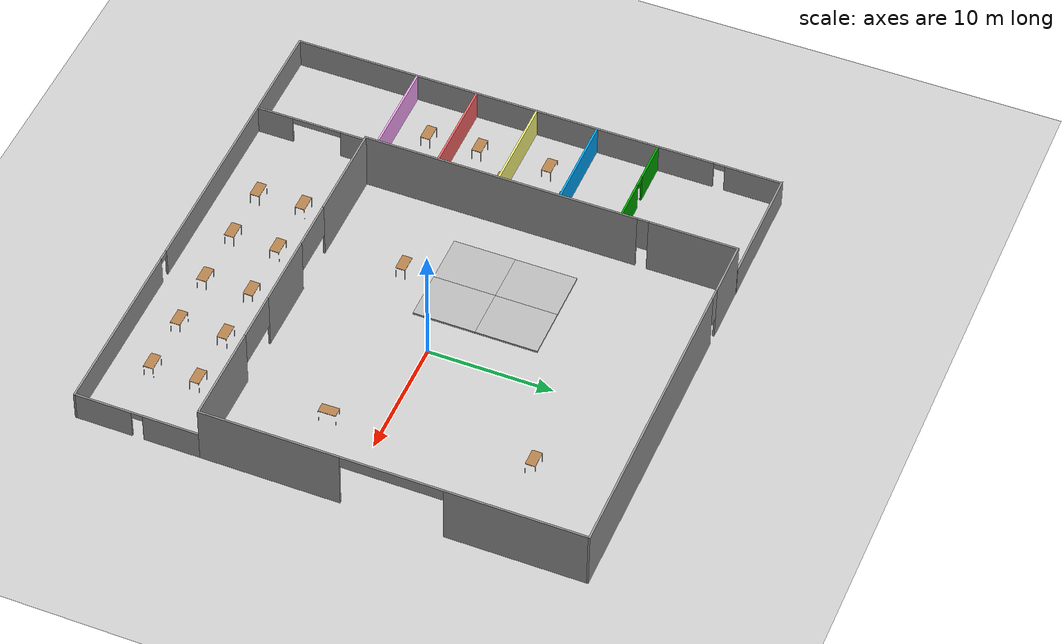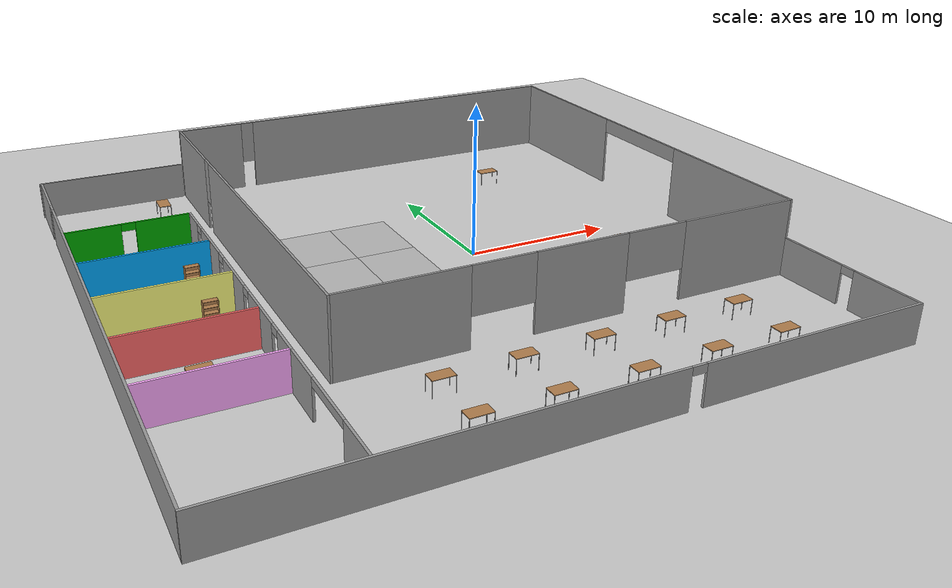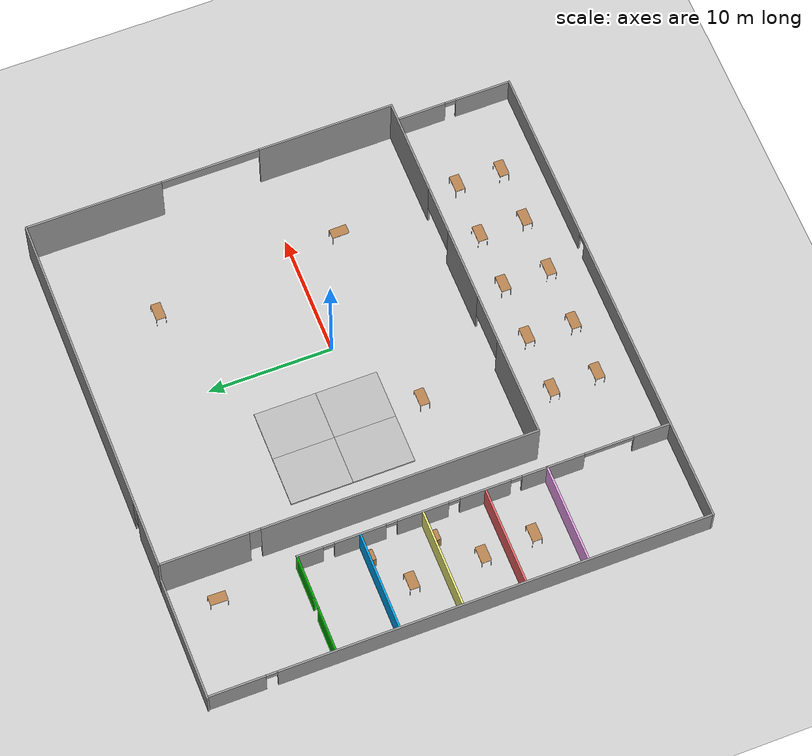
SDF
<sdf version="1.6">
 <world name="default">
  <plugin name="welcome" filename="libwelcome.so"/>
  <light name="sun" type="directional">
   <pose>0 0 10 0 -0 0</pose>
   <diffuse>0.8 0.8 0.8 1</diffuse>
   <specular>0.1 0.1 0.1 1</specular>
   <attenuation>
    <range>1000</range>
    <constant>0.9</constant>
    <linear>0.01</linear>
    <quadratic>0.001</quadratic>
   </attenuation>
   <direction>-0.5 0.5 -1</direction>
  </light>
  <model name="ground_plane">
   <static>1</static>
   <link name="link">
    <collision name="collision">
     <geometry><plane><normal>0 0 1</normal><size>100 100</size></plane></geometry>
     <surface><friction><ode><mu>100</mu><mu2>50</mu2></ode></friction></surface>
    </collision>
    <visual name="visual">
     <cast_shadows>0</cast_shadows>
     <geometry><plane><normal>0 0 1</normal><size>100 100</size></plane></geometry>
     <material>
      <script><uri>file://media/materials/scripts/gazebo.material</uri><name>Gazebo/Grey</name></script>
     </material>
    </visual>
   </link>
  </model>
  <gravity>0 0 -9.8</gravity>
  <magnetic_field>6e-06 2.3e-05 -4.2e-05</magnetic_field>
  <atmosphere type="adiabatic"/>
  <physics name="default_physics" default="0" type="ode">
   <max_step_size>0.001</max_step_size>
   <real_time_factor>1</real_time_factor>
   <real_time_update_rate>1000</real_time_update_rate>
  </physics>
  <scene><ambient>0.4 0.4 0.4 1</ambient><background>0.7 0.7 0.7 1</background><shadows>1</shadows></scene>
  <spherical_coordinates>
   <surface_model>EARTH_WGS84</surface_model>
   <latitude_deg>0</latitude_deg>
   <longitude_deg>0</longitude_deg>
   <elevation>0</elevation>
   <heading_deg>0</heading_deg>
  </spherical_coordinates>
  <model name="robotics_lab">
   <pose>-4.24917 -1.0775 0 0 -0 0</pose>
   <link name="Wall_0">
    <pose>5.0405 20 0 0 -0 0</pose>
    <visual name="Wall_0_Visual_0">
     <pose>-12.7625 0 2.5 0 -0 0</pose>
     <geometry><box><size>4.625 0.15 5</size></box></geometry>
     <material>
      <script><uri>file://media/materials/scripts/gazebo.material</uri><name>Gazebo/Grey</name></script>
      <ambient>0 0 0 1</ambient>
     </material>
    </visual>
    <collision name="Wall_0_Collision_0">
     <geometry><box><size>4.625 0.15 5</size></box></geometry>
     <pose>-12.7625 0 2.5 0 -0 0</pose>
    </collision>
    <visual name="Wall_0_Visual_1">
     <pose>2.7625 0 2.5 0 -0 0</pose>
     <geometry><box><size>24.625 0.15 5</size></box></geometry>
     <material>
      <script><uri>file://media/materials/scripts/gazebo.material</uri><name>Gazebo/Grey</name></script>
      <ambient>0 0 0 1</ambient>
     </material>
    </visual>
    <collision name="Wall_0_Collision_1">
     <geometry><box><size>24.625 0.15 5</size></box></geometry>
     <pose>2.7625 0 2.5 0 -0 0</pose>
    </collision>
    <visual name="Wall_0_Visual_2">
     <pose>-10 0 3.5 0 -0 0</pose>
     <geometry><box><size>0.9 0.15 3</size></box></geometry>
     <material>
      <script><uri>file://media/materials/scripts/gazebo.material</uri><name>Gazebo/Grey</name></script>
      <ambient>0 0 0 1</ambient>
     </material>
    </visual>
    <collision name="Wall_0_Collision_2">
     <geometry><box><size>0.9 0.15 3</size></box></geometry>
     <pose>-10 0 3.5 0 -0 0</pose>
    </collision>
   </link>
   <link name="Wall_10">
    <pose>-19.9595 0 0 0 0 -1.5708</pose>
    <visual name="Wall_10_Visual_0">
     <pose>-17.6875 0 1.25 0 -0 0</pose>
     <geometry><box><size>4.475 0.15 2.5</size></box></geometry>
     <material>
      <script><uri>file://media/materials/scripts/gazebo.material</uri><name>Gazebo/Grey</name></script>
      <ambient>1 1 1 1</ambient>
     </material>
    </visual>
    <collision name="Wall_10_Collision_0">
     <geometry><box><size>4.475 0.15 2.5</size></box></geometry>
     <pose>-17.6875 0 1.25 0 -0 0</pose>
    </collision>
    <visual name="Wall_10_Visual_1">
     <pose>2.6875 0 1.25 0 -0 0</pose>
     <geometry><box><size>34.475 0.15 2.5</size></box></geometry>
     <material>
      <script><uri>file://media/materials/scripts/gazebo.material</uri><name>Gazebo/Grey</name></script>
      <ambient>1 1 1 1</ambient>
     </material>
    </visual>
    <collision name="Wall_10_Collision_1">
     <geometry><box><size>34.475 0.15 2.5</size></box></geometry>
     <pose>2.6875 0 1.25 0 -0 0</pose>
    </collision>
    <visual name="Wall_10_Visual_2">
     <pose>-15 0 2.25 0 -0 0</pose>
     <geometry><box><size>0.9 0.15 0.5</size></box></geometry>
     <material>
      <script><uri>file://media/materials/scripts/gazebo.material</uri><name>Gazebo/Grey</name></script>
      <ambient>1 1 1 1</ambient>
     </material>
    </visual>
    <collision name="Wall_10_Collision_2">
     <geometry><box><size>0.9 0.15 0.5</size></box></geometry>
     <pose>-15 0 2.25 0 -0 0</pose>
    </collision>
   </link>
   <link name="Wall_12">
    <pose>0.040499 -20 0 0 -0 0</pose>
    <visual name="Wall_12_Visual_0">
     <pose>-7.7625 0 1.25 0 -0 0</pose>
     <geometry><box><size>24.625 0.15 2.5</size></box></geometry>
     <material>
      <script><uri>file://media/materials/scripts/gazebo.material</uri><name>Gazebo/Grey</name></script>
      <ambient>1 1 1 1</ambient>
     </material>
    </visual>
    <collision name="Wall_12_Collision_0">
     <geometry><box><size>24.625 0.15 2.5</size></box></geometry>
     <pose>-7.7625 0 1.25 0 -0 0</pose>
    </collision>
    <visual name="Wall_12_Visual_1">
     <pose>12.7625 0 1.25 0 -0 0</pose>
     <geometry><box><size>14.625 0.15 2.5</size></box></geometry>
     <material>
      <script><uri>file://media/materials/scripts/gazebo.material</uri><name>Gazebo/Grey</name></script>
      <ambient>1 1 1 1</ambient>
     </material>
    </visual>
    <collision name="Wall_12_Collision_1">
     <geometry><box><size>14.625 0.15 2.5</size></box></geometry>
     <pose>12.7625 0 1.25 0 -0 0</pose>
    </collision>
    <visual name="Wall_12_Visual_2">
     <pose>5 0 2.25 0 -0 0</pose>
     <geometry><box><size>0.9 0.15 0.5</size></box></geometry>
     <material>
      <script><uri>file://media/materials/scripts/gazebo.material</uri><name>Gazebo/Grey</name></script>
      <ambient>1 1 1 1</ambient>
     </material>
    </visual>
    <collision name="Wall_12_Collision_2">
     <geometry><box><size>0.9 0.15 0.5</size></box></geometry>
     <pose>5 0 2.25 0 -0 0</pose>
    </collision>
   </link>
   <link name="Wall_14">
    <pose>20.0405 -15 0 0 0 -1.5708</pose>
    <visual name="Wall_14_Visual_0">
     <pose>-2.6875 0 1.25 0 -0 0</pose>
     <geometry><box><size>4.475 0.15 2.5</size></box></geometry>
     <material>
      <script><uri>file://media/materials/scripts/gazebo.material</uri><name>Gazebo/Grey</name></script>
      <ambient>1 1 1 1</ambient>
     </material>
    </visual>
    <collision name="Wall_14_Collision_0">
     <geometry><box><size>4.475 0.15 2.5</size></box></geometry>
     <pose>-2.6875 0 1.25 0 -0 0</pose>
    </collision>
    <visual name="Wall_14_Visual_1">
     <pose>2.6875 0 1.25 0 -0 0</pose>
     <geometry><box><size>4.475 0.15 2.5</size></box></geometry>
     <material>
      <script><uri>file://media/materials/scripts/gazebo.material</uri><name>Gazebo/Grey</name></script>
      <ambient>1 1 1 1</ambient>
     </material>
    </visual>
    <collision name="Wall_14_Collision_1">
     <geometry><box><size>4.475 0.15 2.5</size></box></geometry>
     <pose>2.6875 0 1.25 0 -0 0</pose>
    </collision>
    <visual name="Wall_14_Visual_2">
     <pose>0 0 2.25 0 -0 0</pose>
     <geometry><box><size>0.9 0.15 0.5</size></box></geometry>
     <material>
      <script><uri>file://media/materials/scripts/gazebo.material</uri><name>Gazebo/Grey</name></script>
      <ambient>1 1 1 1</ambient>
     </material>
    </visual>
    <collision name="Wall_14_Collision_2">
     <geometry><box><size>0.9 0.15 0.5</size></box></geometry>
     <pose>0 0 2.25 0 -0 0</pose>
    </collision>
   </link>
   <link name="Wall_16">
    <pose>-15.9595 10 0 0 -0 0</pose>
    <visual name="Wall_16_Visual_0">
     <pose>-2.1875 0 1.25 0 -0 0</pose>
     <geometry><box><size>3.475 0.15 2.5</size></box></geometry>
     <material>
      <script><uri>file://media/materials/scripts/gazebo.material</uri><name>Gazebo/Grey</name></script>
      <ambient>0 0.666667 0 1</ambient>
     </material>
    </visual>
    <collision name="Wall_16_Collision_0">
     <geometry><box><size>3.475 0.15 2.5</size></box></geometry>
     <pose>-2.1875 0 1.25 0 -0 0</pose>
    </collision>
    <visual name="Wall_16_Visual_1">
     <pose>2.1875 0 1.25 0 -0 0</pose>
     <geometry><box><size>3.475 0.15 2.5</size></box></geometry>
     <material>
      <script><uri>file://media/materials/scripts/gazebo.material</uri><name>Gazebo/Grey</name></script>
      <ambient>0 0.666667 0 1</ambient>
     </material>
    </visual>
    <collision name="Wall_16_Collision_1">
     <geometry><box><size>3.475 0.15 2.5</size></box></geometry>
     <pose>2.1875 0 1.25 0 -0 0</pose>
    </collision>
    <visual name="Wall_16_Visual_2">
     <pose>-0 0 2.25 0 -0 0</pose>
     <geometry><box><size>0.9 0.15 0.5</size></box></geometry>
     <material>
      <script><uri>file://media/materials/scripts/gazebo.material</uri><name>Gazebo/Grey</name></script>
      <ambient>0 0.666667 0 1</ambient>
     </material>
    </visual>
    <collision name="Wall_16_Collision_2">
     <geometry><box><size>0.9 0.15 0.5</size></box></geometry>
     <pose>-0 0 2.25 0 -0 0</pose>
    </collision>
   </link>
   <link name="Wall_18">
    <collision name="Wall_18_Collision">
     <geometry><box><size>7.85 0.15 2.5</size></box></geometry>
     <pose>0 0 1.25 0 -0 0</pose>
    </collision>
    <visual name="Wall_18_Visual">
     <pose>0 0 1.25 0 -0 0</pose>
     <geometry><box><size>7.85 0.15 2.5</size></box></geometry>
     <material>
      <script><uri>file://media/materials/scripts/gazebo.material</uri><name>Gazebo/Grey</name></script>
      <ambient>0 0.666667 1 1</ambient>
     </material>
    </visual>
    <pose>-15.9595 5 0 0 -0 0</pose>
   </link>
   <link name="Wall_2">
    <pose>20.0405 4.925 0 0 0 -1.5708</pose>
    <visual name="Wall_2_Visual_0">
     <pose>-9.5375 0 2.5 0 -0 0</pose>
     <geometry><box><size>10.925 0.15 5</size></box></geometry>
     <material>
      <script><uri>file://media/materials/scripts/gazebo.material</uri><name>Gazebo/Grey</name></script>
      <ambient>0 0 0 1</ambient>
     </material>
    </visual>
    <collision name="Wall_2_Collision_0">
     <geometry><box><size>10.925 0.15 5</size></box></geometry>
     <pose>-9.5375 0 2.5 0 -0 0</pose>
    </collision>
    <visual name="Wall_2_Visual_1">
     <pose>9.4625 0 2.5 0 -0 0</pose>
     <geometry><box><size>11.075 0.15 5</size></box></geometry>
     <material>
      <script><uri>file://media/materials/scripts/gazebo.material</uri><name>Gazebo/Grey</name></script>
      <ambient>0 0 0 1</ambient>
     </material>
    </visual>
    <collision name="Wall_2_Collision_1">
     <geometry><box><size>11.075 0.15 5</size></box></geometry>
     <pose>9.4625 0 2.5 0 -0 0</pose>
    </collision>
    <visual name="Wall_2_Visual_2">
     <pose>-0.075 0 4.5 0 -0 0</pose>
     <geometry><box><size>8 0.15 1</size></box></geometry>
     <material>
      <script><uri>file://media/materials/scripts/gazebo.material</uri><name>Gazebo/Grey</name></script>
      <ambient>0 0 0 1</ambient>
     </material>
    </visual>
    <collision name="Wall_2_Collision_2">
     <geometry><box><size>8 0.15 1</size></box></geometry>
     <pose>-0.075 0 4.5 0 -0 0</pose>
    </collision>
   </link>
   <link name="Wall_20">
    <collision name="Wall_20_Collision">
     <geometry><box><size>7.85 0.15 2.5</size></box></geometry>
     <pose>0 0 1.25 0 -0 0</pose>
    </collision>
    <visual name="Wall_20_Visual">
     <pose>0 0 1.25 0 -0 0</pose>
     <geometry><box><size>7.85 0.15 2.5</size></box></geometry>
     <material>
      <script><uri>file://media/materials/scripts/gazebo.material</uri><name>Gazebo/Grey</name></script>
      <ambient>1 1 0.498039 1</ambient>
     </material>
    </visual>
    <pose>-15.9595 0 0 0 -0 0</pose>
   </link>
   <link name="Wall_22">
    <collision name="Wall_22_Collision">
     <geometry><box><size>7.85 0.15 2.5</size></box></geometry>
     <pose>0 0 1.25 0 -0 0</pose>
    </collision>
    <visual name="Wall_22_Visual">
     <pose>0 0 1.25 0 -0 0</pose>
     <geometry><box><size>7.85 0.15 2.5</size></box></geometry>
     <material>
      <script><uri>file://media/materials/scripts/gazebo.material</uri><name>Gazebo/Grey</name></script>
      <ambient>1 0.411765 0.411765 1</ambient>
     </material>
    </visual>
    <pose>-15.9595 -5 0 0 -0 0</pose>
   </link>
   <link name="Wall_24">
    <collision name="Wall_24_Collision">
     <geometry><box><size>7.85 0.15 2.5</size></box></geometry>
     <pose>0 0 1.25 0 -0 0</pose>
    </collision>
    <visual name="Wall_24_Visual">
     <pose>0 0 1.25 0 -0 0</pose>
     <geometry><box><size>7.85 0.15 2.5</size></box></geometry>
     <material>
      <script><uri>file://media/materials/scripts/gazebo.material</uri><name>Gazebo/Grey</name></script>
      <ambient>1 0.666667 1 1</ambient>
     </material>
    </visual>
    <pose>-15.9595 -10 0 0 -0 0</pose>
   </link>
   <link name="Wall_26">
    <pose>-11.9595 0 0 0 0 -1.5708</pose>
    <visual name="Wall_26_Visual_0">
     <pose>-9.0125 0 1.25 0 -0 0</pose>
     <geometry><box><size>2.125 0.15 2.5</size></box></geometry>
     <material>
      <script><uri>file://media/materials/scripts/gazebo.material</uri><name>Gazebo/Grey</name></script>
      <ambient>1 1 1 1</ambient>
     </material>
    </visual>
    <collision name="Wall_26_Collision_0">
     <geometry><box><size>2.125 0.15 2.5</size></box></geometry>
     <pose>-9.0125 0 1.25 0 -0 0</pose>
    </collision>
    <visual name="Wall_26_Visual_1">
     <pose>-5 0 1.25 0 -0 0</pose>
     <geometry><box><size>4.1 0.15 2.5</size></box></geometry>
     <material>
      <script><uri>file://media/materials/scripts/gazebo.material</uri><name>Gazebo/Grey</name></script>
      <ambient>1 1 1 1</ambient>
     </material>
    </visual>
    <collision name="Wall_26_Collision_1">
     <geometry><box><size>4.1 0.15 2.5</size></box></geometry>
     <pose>-5 0 1.25 0 -0 0</pose>
    </collision>
    <visual name="Wall_26_Visual_2">
     <pose>0 0 1.25 0 -0 0</pose>
     <geometry><box><size>4.1 0.15 2.5</size></box></geometry>
     <material>
      <script><uri>file://media/materials/scripts/gazebo.material</uri><name>Gazebo/Grey</name></script>
      <ambient>1 1 1 1</ambient>
     </material>
    </visual>
    <collision name="Wall_26_Collision_2">
     <geometry><box><size>4.1 0.15 2.5</size></box></geometry>
     <pose>0 0 1.25 0 -0 0</pose>
    </collision>
    <visual name="Wall_26_Visual_3">
     <pose>5 0 1.25 0 -0 0</pose>
     <geometry><box><size>4.1 0.15 2.5</size></box></geometry>
     <material>
      <script><uri>file://media/materials/scripts/gazebo.material</uri><name>Gazebo/Grey</name></script>
      <ambient>1 1 1 1</ambient>
     </material>
    </visual>
    <collision name="Wall_26_Collision_3">
     <geometry><box><size>4.1 0.15 2.5</size></box></geometry>
     <pose>5 0 1.25 0 -0 0</pose>
    </collision>
    <visual name="Wall_26_Visual_4">
     <pose>9.0125 0 1.25 0 -0 0</pose>
     <geometry><box><size>2.125 0.15 2.5</size></box></geometry>
     <material>
      <script><uri>file://media/materials/scripts/gazebo.material</uri><name>Gazebo/Grey</name></script>
      <ambient>1 1 1 1</ambient>
     </material>
    </visual>
    <collision name="Wall_26_Collision_4">
     <geometry><box><size>2.125 0.15 2.5</size></box></geometry>
     <pose>9.0125 0 1.25 0 -0 0</pose>
    </collision>
    <visual name="Wall_26_Visual_5">
     <pose>-7.5 0 2.25 0 -0 0</pose>
     <geometry><box><size>0.9 0.15 0.5</size></box></geometry>
     <material>
      <script><uri>file://media/materials/scripts/gazebo.material</uri><name>Gazebo/Grey</name></script>
      <ambient>1 1 1 1</ambient>
     </material>
    </visual>
    <collision name="Wall_26_Collision_5">
     <geometry><box><size>0.9 0.15 0.5</size></box></geometry>
     <pose>-7.5 0 2.25 0 -0 0</pose>
    </collision>
    <visual name="Wall_26_Visual_6">
     <pose>-2.5 0 2.25 0 -0 0</pose>
     <geometry><box><size>0.9 0.15 0.5</size></box></geometry>
     <material>
      <script><uri>file://media/materials/scripts/gazebo.material</uri><name>Gazebo/Grey</name></script>
      <ambient>1 1 1 1</ambient>
     </material>
    </visual>
    <collision name="Wall_26_Collision_6">
     <geometry><box><size>0.9 0.15 0.5</size></box></geometry>
     <pose>-2.5 0 2.25 0 -0 0</pose>
    </collision>
    <visual name="Wall_26_Visual_7">
     <pose>2.5 0 2.25 0 -0 0</pose>
     <geometry><box><size>0.9 0.15 0.5</size></box></geometry>
     <material>
      <script><uri>file://media/materials/scripts/gazebo.material</uri><name>Gazebo/Grey</name></script>
      <ambient>1 1 1 1</ambient>
     </material>
    </visual>
    <collision name="Wall_26_Collision_7">
     <geometry><box><size>0.9 0.15 0.5</size></box></geometry>
     <pose>2.5 0 2.25 0 -0 0</pose>
    </collision>
    <visual name="Wall_26_Visual_8">
     <pose>7.5 0 2.25 0 -0 0</pose>
     <geometry><box><size>0.9 0.15 0.5</size></box></geometry>
     <material>
      <script><uri>file://media/materials/scripts/gazebo.material</uri><name>Gazebo/Grey</name></script>
      <ambient>1 1 1 1</ambient>
     </material>
    </visual>
    <collision name="Wall_26_Collision_8">
     <geometry><box><size>0.9 0.15 0.5</size></box></geometry>
     <pose>7.5 0 2.25 0 -0 0</pose>
    </collision>
   </link>
   <link name="Wall_30">
    <pose>-11.9595 -14.925 0 0 0 -1.5708</pose>
    <visual name="Wall_30_Visual_0">
     <pose>-3.4625 0 1.25 0 -0 0</pose>
     <geometry><box><size>3.075 0.15 2.5</size></box></geometry>
     <material>
      <script><uri>file://media/materials/scripts/gazebo.material</uri><name>Gazebo/Grey</name></script>
      <ambient>1 1 1 1</ambient>
     </material>
    </visual>
    <collision name="Wall_30_Collision_0">
     <geometry><box><size>3.075 0.15 2.5</size></box></geometry>
     <pose>-3.4625 0 1.25 0 -0 0</pose>
    </collision>
    <visual name="Wall_30_Visual_1">
     <pose>3.5375 0 1.25 0 -0 0</pose>
     <geometry><box><size>2.925 0.15 2.5</size></box></geometry>
     <material>
      <script><uri>file://media/materials/scripts/gazebo.material</uri><name>Gazebo/Grey</name></script>
      <ambient>1 1 1 1</ambient>
     </material>
    </visual>
    <collision name="Wall_30_Collision_1">
     <geometry><box><size>2.925 0.15 2.5</size></box></geometry>
     <pose>3.5375 0 1.25 0 -0 0</pose>
    </collision>
    <visual name="Wall_30_Visual_2">
     <pose>0.075 0 2.25 0 -0 0</pose>
     <geometry><box><size>4 0.15 0.5</size></box></geometry>
     <material>
      <script><uri>file://media/materials/scripts/gazebo.material</uri><name>Gazebo/Grey</name></script>
      <ambient>1 1 1 1</ambient>
     </material>
    </visual>
    <collision name="Wall_30_Collision_2">
     <geometry><box><size>4 0.15 0.5</size></box></geometry>
     <pose>0.075 0 2.25 0 -0 0</pose>
    </collision>
   </link>
   <link name="Wall_4">
    <pose>5.0405 -10 0 0 -0 0</pose>
    <visual name="Wall_4_Visual_0">
     <pose>-10.9625 0 2.5 0 -0 0</pose>
     <geometry><box><size>7.925 0.15 5</size></box></geometry>
     <material>
      <script><uri>file://media/materials/scripts/gazebo.material</uri><name>Gazebo/Grey</name></script>
      <ambient>0 0 0 1</ambient>
     </material>
    </visual>
    <collision name="Wall_4_Collision_0">
     <geometry><box><size>7.925 0.15 5</size></box></geometry>
     <pose>-10.9625 0 2.5 0 -0 0</pose>
    </collision>
    <visual name="Wall_4_Visual_1">
     <pose>0 0 2.5 0 -0 0</pose>
     <geometry><box><size>6 0.15 5</size></box></geometry>
     <material>
      <script><uri>file://media/materials/scripts/gazebo.material</uri><name>Gazebo/Grey</name></script>
      <ambient>0 0 0 1</ambient>
     </material>
    </visual>
    <collision name="Wall_4_Collision_1">
     <geometry><box><size>6 0.15 5</size></box></geometry>
     <pose>0 0 2.5 0 -0 0</pose>
    </collision>
    <visual name="Wall_4_Visual_2">
     <pose>10.9625 0 2.5 0 -0 0</pose>
     <geometry><box><size>7.925 0.15 5</size></box></geometry>
     <material>
      <script><uri>file://media/materials/scripts/gazebo.material</uri><name>Gazebo/Grey</name></script>
      <ambient>0 0 0 1</ambient>
     </material>
    </visual>
    <collision name="Wall_4_Collision_2">
     <geometry><box><size>7.925 0.15 5</size></box></geometry>
     <pose>10.9625 0 2.5 0 -0 0</pose>
    </collision>
    <visual name="Wall_4_Visual_3">
     <pose>-5 0 3.5 0 -0 0</pose>
     <geometry><box><size>4 0.15 3</size></box></geometry>
     <material>
      <script><uri>file://media/materials/scripts/gazebo.material</uri><name>Gazebo/Grey</name></script>
      <ambient>0 0 0 1</ambient>
     </material>
    </visual>
    <collision name="Wall_4_Collision_3">
     <geometry><box><size>4 0.15 3</size></box></geometry>
     <pose>-5 0 3.5 0 -0 0</pose>
    </collision>
    <visual name="Wall_4_Visual_4">
     <pose>5 0 3.5 0 -0 0</pose>
     <geometry><box><size>4 0.15 3</size></box></geometry>
     <material>
      <script><uri>file://media/materials/scripts/gazebo.material</uri><name>Gazebo/Grey</name></script>
      <ambient>0 0 0 1</ambient>
     </material>
    </visual>
    <collision name="Wall_4_Collision_4">
     <geometry><box><size>4 0.15 3</size></box></geometry>
     <pose>5 0 3.5 0 -0 0</pose>
    </collision>
   </link>
   <link name="Wall_6">
    <pose>-9.9595 4.925 0 0 0 -1.5708</pose>
    <visual name="Wall_6_Visual_0">
     <pose>-11.5125 0 2.5 0 -0 0</pose>
     <geometry><box><size>6.975 0.15 5</size></box></geometry>
     <material>
      <script><uri>file://media/materials/scripts/gazebo.material</uri><name>Gazebo/Grey</name></script>
      <ambient>0 0 0 1</ambient>
     </material>
    </visual>
    <collision name="Wall_6_Collision_0">
     <geometry><box><size>6.975 0.15 5</size></box></geometry>
     <pose>-11.5125 0 2.5 0 -0 0</pose>
    </collision>
    <visual name="Wall_6_Visual_1">
     <pose>3.9375 0 2.5 0 -0 0</pose>
     <geometry><box><size>22.125 0.15 5</size></box></geometry>
     <material>
      <script><uri>file://media/materials/scripts/gazebo.material</uri><name>Gazebo/Grey</name></script>
      <ambient>0 0 0 1</ambient>
     </material>
    </visual>
    <collision name="Wall_6_Collision_1">
     <geometry><box><size>22.125 0.15 5</size></box></geometry>
     <pose>3.9375 0 2.5 0 -0 0</pose>
    </collision>
    <visual name="Wall_6_Visual_2">
     <pose>-7.575 0 3.5 0 -0 0</pose>
     <geometry><box><size>0.9 0.15 3</size></box></geometry>
     <material>
      <script><uri>file://media/materials/scripts/gazebo.material</uri><name>Gazebo/Grey</name></script>
      <ambient>0 0 0 1</ambient>
     </material>
    </visual>
    <collision name="Wall_6_Collision_2">
     <geometry><box><size>0.9 0.15 3</size></box></geometry>
     <pose>-7.575 0 3.5 0 -0 0</pose>
    </collision>
   </link>
   <link name="Wall_8">
    <collision name="Wall_8_Collision">
     <geometry><box><size>10 0.15 2.5</size></box></geometry>
     <pose>0 0 1.25 0 -0 0</pose>
    </collision>
    <visual name="Wall_8_Visual">
     <pose>0 0 1.25 0 -0 0</pose>
     <geometry><box><size>10 0.15 2.5</size></box></geometry>
     <material>
      <script><uri>file://media/materials/scripts/gazebo.material</uri><name>Gazebo/Grey</name></script>
      <ambient>1 1 1 1</ambient>
     </material>
    </visual>
    <pose>-15.1155 20 0 0 -0 0</pose>
   </link>
   <static>1</static>
  </model>
  <model name="bookshelf">
   <static>1</static>
   <link name="link">
    <inertial><mass>1</mass></inertial>
    <collision name="back">
     <pose>0 0.005 0.6 0 -0 0</pose>
     <geometry><box><size>0.9 0.01 1.2</size></box></geometry>
    </collision>
    <visual name="visual1">
     <pose>0 0.005 0.6 0 -0 0</pose>
     <geometry><box><size>0.9 0.01 1.2</size></box></geometry>
     <material>
      <script><uri>file://media/materials/scripts/gazebo.material</uri><name>Gazebo/Wood</name></script>
     </material>
    </visual>
    <collision name="left_side">
     <pose>0.45 -0.195 0.6 0 -0 0</pose>
     <geometry><box><size>0.02 0.4 1.2</size></box></geometry>
    </collision>
    <visual name="visual2">
     <pose>0.45 -0.195 0.6 0 -0 0</pose>
     <geometry><box><size>0.02 0.4 1.2</size></box></geometry>
     <material>
      <script><uri>file://media/materials/scripts/gazebo.material</uri><name>Gazebo/Wood</name></script>
     </material>
    </visual>
    <collision name="right_side">
     <pose>-0.45 -0.195 0.6 0 -0 0</pose>
     <geometry><box><size>0.02 0.4 1.2</size></box></geometry>
    </collision>
    <visual name="visual3">
     <pose>-0.45 -0.195 0.6 0 -0 0</pose>
     <geometry><box><size>0.02 0.4 1.2</size></box></geometry>
     <material>
      <script><uri>file://media/materials/scripts/gazebo.material</uri><name>Gazebo/Wood</name></script>
     </material>
    </visual>
    <collision name="bottom">
     <pose>0 -0.195 0.03 0 -0 0</pose>
     <geometry><box><size>0.88 0.4 0.06</size></box></geometry>
    </collision>
    <visual name="visual4">
     <pose>0 -0.195 0.03 0 -0 0</pose>
     <geometry><box><size>0.88 0.4 0.06</size></box></geometry>
     <material>
      <script><uri>file://media/materials/scripts/gazebo.material</uri><name>Gazebo/Wood</name></script>
     </material>
    </visual>
    <collision name="top">
     <pose>0 -0.195 1.19 0 -0 0</pose>
     <geometry><box><size>0.88 0.4 0.02</size></box></geometry>
    </collision>
    <visual name="visual5">
     <pose>0 -0.195 1.19 0 -0 0</pose>
     <geometry><box><size>0.88 0.4 0.02</size></box></geometry>
     <material>
      <script><uri>file://media/materials/scripts/gazebo.material</uri><name>Gazebo/Wood</name></script>
     </material>
    </visual>
    <collision name="low_shelf">
     <pose>0 -0.195 0.43 0 -0 0</pose>
     <geometry><box><size>0.88 0.4 0.02</size></box></geometry>
    </collision>
    <visual name="visual6">
     <pose>0 -0.195 0.43 0 -0 0</pose>
     <geometry><box><size>0.88 0.4 0.02</size></box></geometry>
     <material>
      <script><uri>file://media/materials/scripts/gazebo.material</uri><name>Gazebo/Wood</name></script>
     </material>
    </visual>
    <collision name="high_shelf">
     <pose>0 -0.195 0.8 0 -0 0</pose>
     <geometry><box><size>0.88 0.4 0.02</size></box></geometry>
    </collision>
    <visual name="visual7">
     <pose>0 -0.195 0.8 0 -0 0</pose>
     <geometry><box><size>0.88 0.4 0.02</size></box></geometry>
     <material>
      <script><uri>file://media/materials/scripts/gazebo.material</uri><name>Gazebo/Wood</name></script>
     </material>
    </visual>
   </link>
   <pose>-17.5864 3.74248 0 0 -0 0</pose>
  </model>
  <model name="table">
   <static>0</static>
   <link name="link">
    <collision name="surface">
     <pose>0 0 1 0 -0 0</pose>
     <geometry><box><size>1.5 0.8 0.03</size></box></geometry>
     <surface><friction><ode><mu>0.6</mu><mu2>0.6</mu2></ode></friction></surface>
    </collision>
    <visual name="visual1">
     <pose>0 0 1 0 -0 0</pose>
     <geometry><box><size>1.4 0.8 0.04</size></box></geometry>
     <material>
      <script><uri>file://media/materials/scripts/gazebo.material</uri><name>Gazebo/Wood</name></script>
     </material>
    </visual>
    <collision name="front_left_leg">
     <pose>0.68 0.38 0.5 0 -0 0</pose>
     <geometry><cylinder><radius>0.02</radius><length>1</length></cylinder></geometry>
    </collision>
    <visual name="front_left_leg">
     <pose>0.68 0.38 0.5 0 -0 0</pose>
     <geometry><cylinder><radius>0.02</radius><length>1</length></cylinder></geometry>
     <material>
      <script><uri>file://media/materials/scripts/gazebo.material</uri><name>Gazebo/Grey</name></script>
     </material>
    </visual>
    <collision name="front_right_leg">
     <pose>0.68 -0.38 0.5 0 -0 0</pose>
     <geometry><cylinder><radius>0.02</radius><length>1</length></cylinder></geometry>
    </collision>
    <visual name="front_right_leg">
     <pose>0.68 -0.38 0.5 0 -0 0</pose>
     <geometry><cylinder><radius>0.02</radius><length>1</length></cylinder></geometry>
     <material>
      <script><uri>file://media/materials/scripts/gazebo.material</uri><name>Gazebo/Grey</name></script>
     </material>
    </visual>
    <collision name="back_right_leg">
     <pose>-0.68 -0.38 0.5 0 -0 0</pose>
     <geometry><cylinder><radius>0.02</radius><length>1</length></cylinder></geometry>
    </collision>
    <visual name="back_right_leg">
     <pose>-0.68 -0.38 0.5 0 -0 0</pose>
     <geometry><cylinder><radius>0.02</radius><length>1</length></cylinder></geometry>
     <material>
      <script><uri>file://media/materials/scripts/gazebo.material</uri><name>Gazebo/Grey</name></script>
     </material>
    </visual>
    <collision name="back_left_leg">
     <pose>-0.68 0.38 0.5 0 -0 0</pose>
     <geometry><cylinder><radius>0.02</radius><length>1</length></cylinder></geometry>
    </collision>
    <visual name="back_left_leg">
     <pose>-0.68 0.38 0.5 0 -0 0</pose>
     <geometry><cylinder><radius>0.02</radius><length>1</length></cylinder></geometry>
     <material>
      <script><uri>file://media/materials/scripts/gazebo.material</uri><name>Gazebo/Grey</name></script>
     </material>
    </visual>
    <inertial>
     <inertia><ixx>1</ixx><ixy>0</ixy><ixz>0</ixz><iyy>1</iyy><iyz>0</iyz><izz>1</izz></inertia>
     <mass>1</mass>
    </inertial>
   </link>
   <pose>-9.57196 -14.2734 -1e-06 0 1e-06 0</pose>
  </model>
  <model name="table_clone">
   <static>0</static>
   <link name="link">
    <collision name="surface">
     <pose>0 0 1 0 -0 0</pose>
     <geometry><box><size>1.5 0.8 0.03</size></box></geometry>
     <surface><friction><ode><mu>0.6</mu><mu2>0.6</mu2></ode></friction></surface>
    </collision>
    <visual name="visual1">
     <pose>0 0 1 0 -0 0</pose>
     <geometry><box><size>1.4 0.8 0.04</size></box></geometry>
     <material>
      <script><uri>file://media/materials/scripts/gazebo.material</uri><name>Gazebo/Wood</name></script>
     </material>
    </visual>
    <collision name="front_left_leg">
     <pose>0.68 0.38 0.5 0 -0 0</pose>
     <geometry><cylinder><radius>0.02</radius><length>1</length></cylinder></geometry>
    </collision>
    <visual name="front_left_leg">
     <pose>0.68 0.38 0.5 0 -0 0</pose>
     <geometry><cylinder><radius>0.02</radius><length>1</length></cylinder></geometry>
     <material>
      <script><uri>file://media/materials/scripts/gazebo.material</uri><name>Gazebo/Grey</name></script>
     </material>
    </visual>
    <collision name="front_right_leg">
     <pose>0.68 -0.38 0.5 0 -0 0</pose>
     <geometry><cylinder><radius>0.02</radius><length>1</length></cylinder></geometry>
    </collision>
    <visual name="front_right_leg">
     <pose>0.68 -0.38 0.5 0 -0 0</pose>
     <geometry><cylinder><radius>0.02</radius><length>1</length></cylinder></geometry>
     <material>
      <script><uri>file://media/materials/scripts/gazebo.material</uri><name>Gazebo/Grey</name></script>
     </material>
    </visual>
    <collision name="back_right_leg">
     <pose>-0.68 -0.38 0.5 0 -0 0</pose>
     <geometry><cylinder><radius>0.02</radius><length>1</length></cylinder></geometry>
    </collision>
    <visual name="back_right_leg">
     <pose>-0.68 -0.38 0.5 0 -0 0</pose>
     <geometry><cylinder><radius>0.02</radius><length>1</length></cylinder></geometry>
     <material>
      <script><uri>file://media/materials/scripts/gazebo.material</uri><name>Gazebo/Grey</name></script>
     </material>
    </visual>
    <collision name="back_left_leg">
     <pose>-0.68 0.38 0.5 0 -0 0</pose>
     <geometry><cylinder><radius>0.02</radius><length>1</length></cylinder></geometry>
    </collision>
    <visual name="back_left_leg">
     <pose>-0.68 0.38 0.5 0 -0 0</pose>
     <geometry><cylinder><radius>0.02</radius><length>1</length></cylinder></geometry>
     <material>
      <script><uri>file://media/materials/scripts/gazebo.material</uri><name>Gazebo/Grey</name></script>
     </material>
    </visual>
    <inertial>
     <inertia><ixx>1</ixx><ixy>0</ixy><ixz>0</ixz><iyy>1</iyy><iyz>0</iyz><izz>1</izz></inertia>
     <mass>1</mass>
    </inertial>
   </link>
   <pose>-20.4894 1.48775 -8e-06 0 -0 0</pose>
  </model>
  <model name="table_clone_clone">
   <static>0</static>
   <link name="link">
    <collision name="surface">
     <pose>0 0 1 0 -0 0</pose>
     <geometry><box><size>1.5 0.8 0.03</size></box></geometry>
     <surface><friction><ode><mu>0.6</mu><mu2>0.6</mu2></ode></friction></surface>
    </collision>
    <visual name="visual1">
     <pose>0 0 1 0 -0 0</pose>
     <geometry><box><size>1.4 0.8 0.04</size></box></geometry>
     <material>
      <script><uri>file://media/materials/scripts/gazebo.material</uri><name>Gazebo/Wood</name></script>
     </material>
    </visual>
    <collision name="front_left_leg">
     <pose>0.68 0.38 0.5 0 -0 0</pose>
     <geometry><cylinder><radius>0.02</radius><length>1</length></cylinder></geometry>
    </collision>
    <visual name="front_left_leg">
     <pose>0.68 0.38 0.5 0 -0 0</pose>
     <geometry><cylinder><radius>0.02</radius><length>1</length></cylinder></geometry>
     <material>
      <script><uri>file://media/materials/scripts/gazebo.material</uri><name>Gazebo/Grey</name></script>
     </material>
    </visual>
    <collision name="front_right_leg">
     <pose>0.68 -0.38 0.5 0 -0 0</pose>
     <geometry><cylinder><radius>0.02</radius><length>1</length></cylinder></geometry>
    </collision>
    <visual name="front_right_leg">
     <pose>0.68 -0.38 0.5 0 -0 0</pose>
     <geometry><cylinder><radius>0.02</radius><length>1</length></cylinder></geometry>
     <material>
      <script><uri>file://media/materials/scripts/gazebo.material</uri><name>Gazebo/Grey</name></script>
     </material>
    </visual>
    <collision name="back_right_leg">
     <pose>-0.68 -0.38 0.5 0 -0 0</pose>
     <geometry><cylinder><radius>0.02</radius><length>1</length></cylinder></geometry>
    </collision>
    <visual name="back_right_leg">
     <pose>-0.68 -0.38 0.5 0 -0 0</pose>
     <geometry><cylinder><radius>0.02</radius><length>1</length></cylinder></geometry>
     <material>
      <script><uri>file://media/materials/scripts/gazebo.material</uri><name>Gazebo/Grey</name></script>
     </material>
    </visual>
    <collision name="back_left_leg">
     <pose>-0.68 0.38 0.5 0 -0 0</pose>
     <geometry><cylinder><radius>0.02</radius><length>1</length></cylinder></geometry>
    </collision>
    <visual name="back_left_leg">
     <pose>-0.68 0.38 0.5 0 -0 0</pose>
     <geometry><cylinder><radius>0.02</radius><length>1</length></cylinder></geometry>
     <material>
      <script><uri>file://media/materials/scripts/gazebo.material</uri><name>Gazebo/Grey</name></script>
     </material>
    </visual>
    <inertial>
     <inertia><ixx>1</ixx><ixy>0</ixy><ixz>0</ixz><iyy>1</iyy><iyz>0</iyz><izz>1</izz></inertia>
     <mass>1</mass>
    </inertial>
   </link>
   <pose>-20.428 -4.24602 -1e-06 0 1e-06 0</pose>
  </model>
  <model name="bookshelf_clone">
   <static>1</static>
   <link name="link">
    <inertial><mass>1</mass></inertial>
    <collision name="back">
     <pose>0 0.005 0.6 0 -0 0</pose>
     <geometry><box><size>0.9 0.01 1.2</size></box></geometry>
    </collision>
    <visual name="visual1">
     <pose>0 0.005 0.6 0 -0 0</pose>
     <geometry><box><size>0.9 0.01 1.2</size></box></geometry>
     <material>
      <script><uri>file://media/materials/scripts/gazebo.material</uri><name>Gazebo/Wood</name></script>
     </material>
    </visual>
    <collision name="left_side">
     <pose>0.45 -0.195 0.6 0 -0 0</pose>
     <geometry><box><size>0.02 0.4 1.2</size></box></geometry>
    </collision>
    <visual name="visual2">
     <pose>0.45 -0.195 0.6 0 -0 0</pose>
     <geometry><box><size>0.02 0.4 1.2</size></box></geometry>
     <material>
      <script><uri>file://media/materials/scripts/gazebo.material</uri><name>Gazebo/Wood</name></script>
     </material>
    </visual>
    <collision name="right_side">
     <pose>-0.45 -0.195 0.6 0 -0 0</pose>
     <geometry><box><size>0.02 0.4 1.2</size></box></geometry>
    </collision>
    <visual name="visual3">
     <pose>-0.45 -0.195 0.6 0 -0 0</pose>
     <geometry><box><size>0.02 0.4 1.2</size></box></geometry>
     <material>
      <script><uri>file://media/materials/scripts/gazebo.material</uri><name>Gazebo/Wood</name></script>
     </material>
    </visual>
    <collision name="bottom">
     <pose>0 -0.195 0.03 0 -0 0</pose>
     <geometry><box><size>0.88 0.4 0.06</size></box></geometry>
    </collision>
    <visual name="visual4">
     <pose>0 -0.195 0.03 0 -0 0</pose>
     <geometry><box><size>0.88 0.4 0.06</size></box></geometry>
     <material>
      <script><uri>file://media/materials/scripts/gazebo.material</uri><name>Gazebo/Wood</name></script>
     </material>
    </visual>
    <collision name="top">
     <pose>0 -0.195 1.19 0 -0 0</pose>
     <geometry><box><size>0.88 0.4 0.02</size></box></geometry>
    </collision>
    <visual name="visual5">
     <pose>0 -0.195 1.19 0 -0 0</pose>
     <geometry><box><size>0.88 0.4 0.02</size></box></geometry>
     <material>
      <script><uri>file://media/materials/scripts/gazebo.material</uri><name>Gazebo/Wood</name></script>
     </material>
    </visual>
    <collision name="low_shelf">
     <pose>0 -0.195 0.43 0 -0 0</pose>
     <geometry><box><size>0.88 0.4 0.02</size></box></geometry>
    </collision>
    <visual name="visual6">
     <pose>0 -0.195 0.43 0 -0 0</pose>
     <geometry><box><size>0.88 0.4 0.02</size></box></geometry>
     <material>
      <script><uri>file://media/materials/scripts/gazebo.material</uri><name>Gazebo/Wood</name></script>
     </material>
    </visual>
    <collision name="high_shelf">
     <pose>0 -0.195 0.8 0 -0 0</pose>
     <geometry><box><size>0.88 0.4 0.02</size></box></geometry>
    </collision>
    <visual name="visual7">
     <pose>0 -0.195 0.8 0 -0 0</pose>
     <geometry><box><size>0.88 0.4 0.02</size></box></geometry>
     <material>
      <script><uri>file://media/materials/scripts/gazebo.material</uri><name>Gazebo/Wood</name></script>
     </material>
    </visual>
   </link>
   <pose>-17.8107 -1.34235 0 0 -0 0</pose>
  </model>
  <model name="table_clone_0">
   <static>0</static>
   <link name="link">
    <collision name="surface">
     <pose>0 0 1 0 -0 0</pose>
     <geometry><box><size>1.5 0.8 0.03</size></box></geometry>
     <surface><friction><ode><mu>0.6</mu><mu2>0.6</mu2></ode></friction></surface>
    </collision>
    <visual name="visual1">
     <pose>0 0 1 0 -0 0</pose>
     <geometry><box><size>1.4 0.8 0.04</size></box></geometry>
     <material>
      <script><uri>file://media/materials/scripts/gazebo.material</uri><name>Gazebo/Wood</name></script>
     </material>
    </visual>
    <collision name="front_left_leg">
     <pose>0.68 0.38 0.5 0 -0 0</pose>
     <geometry><cylinder><radius>0.02</radius><length>1</length></cylinder></geometry>
    </collision>
    <visual name="front_left_leg">
     <pose>0.68 0.38 0.5 0 -0 0</pose>
     <geometry><cylinder><radius>0.02</radius><length>1</length></cylinder></geometry>
     <material>
      <script><uri>file://media/materials/scripts/gazebo.material</uri><name>Gazebo/Grey</name></script>
     </material>
    </visual>
    <collision name="front_right_leg">
     <pose>0.68 -0.38 0.5 0 -0 0</pose>
     <geometry><cylinder><radius>0.02</radius><length>1</length></cylinder></geometry>
    </collision>
    <visual name="front_right_leg">
     <pose>0.68 -0.38 0.5 0 -0 0</pose>
     <geometry><cylinder><radius>0.02</radius><length>1</length></cylinder></geometry>
     <material>
      <script><uri>file://media/materials/scripts/gazebo.material</uri><name>Gazebo/Grey</name></script>
     </material>
    </visual>
    <collision name="back_right_leg">
     <pose>-0.68 -0.38 0.5 0 -0 0</pose>
     <geometry><cylinder><radius>0.02</radius><length>1</length></cylinder></geometry>
    </collision>
    <visual name="back_right_leg">
     <pose>-0.68 -0.38 0.5 0 -0 0</pose>
     <geometry><cylinder><radius>0.02</radius><length>1</length></cylinder></geometry>
     <material>
      <script><uri>file://media/materials/scripts/gazebo.material</uri><name>Gazebo/Grey</name></script>
     </material>
    </visual>
    <collision name="back_left_leg">
     <pose>-0.68 0.38 0.5 0 -0 0</pose>
     <geometry><cylinder><radius>0.02</radius><length>1</length></cylinder></geometry>
    </collision>
    <visual name="back_left_leg">
     <pose>-0.68 0.38 0.5 0 -0 0</pose>
     <geometry><cylinder><radius>0.02</radius><length>1</length></cylinder></geometry>
     <material>
      <script><uri>file://media/materials/scripts/gazebo.material</uri><name>Gazebo/Grey</name></script>
     </material>
    </visual>
    <inertial>
     <inertia><ixx>1</ixx><ixy>0</ixy><ixz>0</ixz><iyy>1</iyy><iyz>0</iyz><izz>1</izz></inertia>
     <mass>1</mass>
    </inertial>
   </link>
   <pose>-20.1857 -8.43233 -1e-06 0 1e-06 0</pose>
  </model>
  <model name="table_clone_1">
   <static>0</static>
   <link name="link">
    <collision name="surface">
     <pose>0 0 1 0 -0 0</pose>
     <geometry><box><size>1.5 0.8 0.03</size></box></geometry>
     <surface><friction><ode><mu>0.6</mu><mu2>0.6</mu2></ode></friction></surface>
    </collision>
    <visual name="visual1">
     <pose>0 0 1 0 -0 0</pose>
     <geometry><box><size>1.4 0.8 0.04</size></box></geometry>
     <material>
      <script><uri>file://media/materials/scripts/gazebo.material</uri><name>Gazebo/Wood</name></script>
     </material>
    </visual>
    <collision name="front_left_leg">
     <pose>0.68 0.38 0.5 0 -0 0</pose>
     <geometry><cylinder><radius>0.02</radius><length>1</length></cylinder></geometry>
    </collision>
    <visual name="front_left_leg">
     <pose>0.68 0.38 0.5 0 -0 0</pose>
     <geometry><cylinder><radius>0.02</radius><length>1</length></cylinder></geometry>
     <material>
      <script><uri>file://media/materials/scripts/gazebo.material</uri><name>Gazebo/Grey</name></script>
     </material>
    </visual>
    <collision name="front_right_leg">
     <pose>0.68 -0.38 0.5 0 -0 0</pose>
     <geometry><cylinder><radius>0.02</radius><length>1</length></cylinder></geometry>
    </collision>
    <visual name="front_right_leg">
     <pose>0.68 -0.38 0.5 0 -0 0</pose>
     <geometry><cylinder><radius>0.02</radius><length>1</length></cylinder></geometry>
     <material>
      <script><uri>file://media/materials/scripts/gazebo.material</uri><name>Gazebo/Grey</name></script>
     </material>
    </visual>
    <collision name="back_right_leg">
     <pose>-0.68 -0.38 0.5 0 -0 0</pose>
     <geometry><cylinder><radius>0.02</radius><length>1</length></cylinder></geometry>
    </collision>
    <visual name="back_right_leg">
     <pose>-0.68 -0.38 0.5 0 -0 0</pose>
     <geometry><cylinder><radius>0.02</radius><length>1</length></cylinder></geometry>
     <material>
      <script><uri>file://media/materials/scripts/gazebo.material</uri><name>Gazebo/Grey</name></script>
     </material>
    </visual>
    <collision name="back_left_leg">
     <pose>-0.68 0.38 0.5 0 -0 0</pose>
     <geometry><cylinder><radius>0.02</radius><length>1</length></cylinder></geometry>
    </collision>
    <visual name="back_left_leg">
     <pose>-0.68 0.38 0.5 0 -0 0</pose>
     <geometry><cylinder><radius>0.02</radius><length>1</length></cylinder></geometry>
     <material>
      <script><uri>file://media/materials/scripts/gazebo.material</uri><name>Gazebo/Grey</name></script>
     </material>
    </visual>
    <inertial>
     <inertia><ixx>1</ixx><ixy>0</ixy><ixz>0</ixz><iyy>1</iyy><iyz>0</iyz><izz>1</izz></inertia>
     <mass>1</mass>
    </inertial>
   </link>
   <pose>-9.50655 -18.0093 -1e-06 0 1e-06 0</pose>
  </model>
  <model name="table_clone_2">
   <static>0</static>
   <link name="link">
    <collision name="surface">
     <pose>0 0 1 0 -0 0</pose>
     <geometry><box><size>1.5 0.8 0.03</size></box></geometry>
     <surface><friction><ode><mu>0.6</mu><mu2>0.6</mu2></ode></friction></surface>
    </collision>
    <visual name="visual1">
     <pose>0 0 1 0 -0 0</pose>
     <geometry><box><size>1.4 0.8 0.04</size></box></geometry>
     <material>
      <script><uri>file://media/materials/scripts/gazebo.material</uri><name>Gazebo/Wood</name></script>
     </material>
    </visual>
    <collision name="front_left_leg">
     <pose>0.68 0.38 0.5 0 -0 0</pose>
     <geometry><cylinder><radius>0.02</radius><length>1</length></cylinder></geometry>
    </collision>
    <visual name="front_left_leg">
     <pose>0.68 0.38 0.5 0 -0 0</pose>
     <geometry><cylinder><radius>0.02</radius><length>1</length></cylinder></geometry>
     <material>
      <script><uri>file://media/materials/scripts/gazebo.material</uri><name>Gazebo/Grey</name></script>
     </material>
    </visual>
    <collision name="front_right_leg">
     <pose>0.68 -0.38 0.5 0 -0 0</pose>
     <geometry><cylinder><radius>0.02</radius><length>1</length></cylinder></geometry>
    </collision>
    <visual name="front_right_leg">
     <pose>0.68 -0.38 0.5 0 -0 0</pose>
     <geometry><cylinder><radius>0.02</radius><length>1</length></cylinder></geometry>
     <material>
      <script><uri>file://media/materials/scripts/gazebo.material</uri><name>Gazebo/Grey</name></script>
     </material>
    </visual>
    <collision name="back_right_leg">
     <pose>-0.68 -0.38 0.5 0 -0 0</pose>
     <geometry><cylinder><radius>0.02</radius><length>1</length></cylinder></geometry>
    </collision>
    <visual name="back_right_leg">
     <pose>-0.68 -0.38 0.5 0 -0 0</pose>
     <geometry><cylinder><radius>0.02</radius><length>1</length></cylinder></geometry>
     <material>
      <script><uri>file://media/materials/scripts/gazebo.material</uri><name>Gazebo/Grey</name></script>
     </material>
    </visual>
    <collision name="back_left_leg">
     <pose>-0.68 0.38 0.5 0 -0 0</pose>
     <geometry><cylinder><radius>0.02</radius><length>1</length></cylinder></geometry>
    </collision>
    <visual name="back_left_leg">
     <pose>-0.68 0.38 0.5 0 -0 0</pose>
     <geometry><cylinder><radius>0.02</radius><length>1</length></cylinder></geometry>
     <material>
      <script><uri>file://media/materials/scripts/gazebo.material</uri><name>Gazebo/Grey</name></script>
     </material>
    </visual>
    <inertial>
     <inertia><ixx>1</ixx><ixy>0</ixy><ixz>0</ixz><iyy>1</iyy><iyz>0</iyz><izz>1</izz></inertia>
     <mass>1</mass>
    </inertial>
   </link>
   <pose>-4.73326 -14.2156 -1e-06 0 1e-06 0</pose>
  </model>
  <model name="table_clone_3">
   <static>0</static>
   <link name="link">
    <collision name="surface">
     <pose>0 0 1 0 -0 0</pose>
     <geometry><box><size>1.5 0.8 0.03</size></box></geometry>
     <surface><friction><ode><mu>0.6</mu><mu2>0.6</mu2></ode></friction></surface>
    </collision>
    <visual name="visual1">
     <pose>0 0 1 0 -0 0</pose>
     <geometry><box><size>1.4 0.8 0.04</size></box></geometry>
     <material>
      <script><uri>file://media/materials/scripts/gazebo.material</uri><name>Gazebo/Wood</name></script>
     </material>
    </visual>
    <collision name="front_left_leg">
     <pose>0.68 0.38 0.5 0 -0 0</pose>
     <geometry><cylinder><radius>0.02</radius><length>1</length></cylinder></geometry>
    </collision>
    <visual name="front_left_leg">
     <pose>0.68 0.38 0.5 0 -0 0</pose>
     <geometry><cylinder><radius>0.02</radius><length>1</length></cylinder></geometry>
     <material>
      <script><uri>file://media/materials/scripts/gazebo.material</uri><name>Gazebo/Grey</name></script>
     </material>
    </visual>
    <collision name="front_right_leg">
     <pose>0.68 -0.38 0.5 0 -0 0</pose>
     <geometry><cylinder><radius>0.02</radius><length>1</length></cylinder></geometry>
    </collision>
    <visual name="front_right_leg">
     <pose>0.68 -0.38 0.5 0 -0 0</pose>
     <geometry><cylinder><radius>0.02</radius><length>1</length></cylinder></geometry>
     <material>
      <script><uri>file://media/materials/scripts/gazebo.material</uri><name>Gazebo/Grey</name></script>
     </material>
    </visual>
    <collision name="back_right_leg">
     <pose>-0.68 -0.38 0.5 0 -0 0</pose>
     <geometry><cylinder><radius>0.02</radius><length>1</length></cylinder></geometry>
    </collision>
    <visual name="back_right_leg">
     <pose>-0.68 -0.38 0.5 0 -0 0</pose>
     <geometry><cylinder><radius>0.02</radius><length>1</length></cylinder></geometry>
     <material>
      <script><uri>file://media/materials/scripts/gazebo.material</uri><name>Gazebo/Grey</name></script>
     </material>
    </visual>
    <collision name="back_left_leg">
     <pose>-0.68 0.38 0.5 0 -0 0</pose>
     <geometry><cylinder><radius>0.02</radius><length>1</length></cylinder></geometry>
    </collision>
    <visual name="back_left_leg">
     <pose>-0.68 0.38 0.5 0 -0 0</pose>
     <geometry><cylinder><radius>0.02</radius><length>1</length></cylinder></geometry>
     <material>
      <script><uri>file://media/materials/scripts/gazebo.material</uri><name>Gazebo/Grey</name></script>
     </material>
    </visual>
    <inertial>
     <inertia><ixx>1</ixx><ixy>0</ixy><ixz>0</ixz><iyy>1</iyy><iyz>0</iyz><izz>1</izz></inertia>
     <mass>1</mass>
    </inertial>
   </link>
   <pose>-4.8651 -18.0156 -1e-06 0 1e-06 0</pose>
  </model>
  <model name="table_clone_4">
   <static>0</static>
   <link name="link">
    <collision name="surface">
     <pose>0 0 1 0 -0 0</pose>
     <geometry><box><size>1.5 0.8 0.03</size></box></geometry>
     <surface><friction><ode><mu>0.6</mu><mu2>0.6</mu2></ode></friction></surface>
    </collision>
    <visual name="visual1">
     <pose>0 0 1 0 -0 0</pose>
     <geometry><box><size>1.4 0.8 0.04</size></box></geometry>
     <material>
      <script><uri>file://media/materials/scripts/gazebo.material</uri><name>Gazebo/Wood</name></script>
     </material>
    </visual>
    <collision name="front_left_leg">
     <pose>0.68 0.38 0.5 0 -0 0</pose>
     <geometry><cylinder><radius>0.02</radius><length>1</length></cylinder></geometry>
    </collision>
    <visual name="front_left_leg">
     <pose>0.68 0.38 0.5 0 -0 0</pose>
     <geometry><cylinder><radius>0.02</radius><length>1</length></cylinder></geometry>
     <material>
      <script><uri>file://media/materials/scripts/gazebo.material</uri><name>Gazebo/Grey</name></script>
     </material>
    </visual>
    <collision name="front_right_leg">
     <pose>0.68 -0.38 0.5 0 -0 0</pose>
     <geometry><cylinder><radius>0.02</radius><length>1</length></cylinder></geometry>
    </collision>
    <visual name="front_right_leg">
     <pose>0.68 -0.38 0.5 0 -0 0</pose>
     <geometry><cylinder><radius>0.02</radius><length>1</length></cylinder></geometry>
     <material>
      <script><uri>file://media/materials/scripts/gazebo.material</uri><name>Gazebo/Grey</name></script>
     </material>
    </visual>
    <collision name="back_right_leg">
     <pose>-0.68 -0.38 0.5 0 -0 0</pose>
     <geometry><cylinder><radius>0.02</radius><length>1</length></cylinder></geometry>
    </collision>
    <visual name="back_right_leg">
     <pose>-0.68 -0.38 0.5 0 -0 0</pose>
     <geometry><cylinder><radius>0.02</radius><length>1</length></cylinder></geometry>
     <material>
      <script><uri>file://media/materials/scripts/gazebo.material</uri><name>Gazebo/Grey</name></script>
     </material>
    </visual>
    <collision name="back_left_leg">
     <pose>-0.68 0.38 0.5 0 -0 0</pose>
     <geometry><cylinder><radius>0.02</radius><length>1</length></cylinder></geometry>
    </collision>
    <visual name="back_left_leg">
     <pose>-0.68 0.38 0.5 0 -0 0</pose>
     <geometry><cylinder><radius>0.02</radius><length>1</length></cylinder></geometry>
     <material>
      <script><uri>file://media/materials/scripts/gazebo.material</uri><name>Gazebo/Grey</name></script>
     </material>
    </visual>
    <inertial>
     <inertia><ixx>1</ixx><ixy>0</ixy><ixz>0</ixz><iyy>1</iyy><iyz>0</iyz><izz>1</izz></inertia>
     <mass>1</mass>
    </inertial>
   </link>
   <pose>0.087077 -18.0097 -1e-06 0 1e-06 0</pose>
  </model>
  <model name="table_clone_5">
   <static>0</static>
   <link name="link">
    <collision name="surface">
     <pose>0 0 1 0 -0 0</pose>
     <geometry><box><size>1.5 0.8 0.03</size></box></geometry>
     <surface><friction><ode><mu>0.6</mu><mu2>0.6</mu2></ode></friction></surface>
    </collision>
    <visual name="visual1">
     <pose>0 0 1 0 -0 0</pose>
     <geometry><box><size>1.4 0.8 0.04</size></box></geometry>
     <material>
      <script><uri>file://media/materials/scripts/gazebo.material</uri><name>Gazebo/Wood</name></script>
     </material>
    </visual>
    <collision name="front_left_leg">
     <pose>0.68 0.38 0.5 0 -0 0</pose>
     <geometry><cylinder><radius>0.02</radius><length>1</length></cylinder></geometry>
    </collision>
    <visual name="front_left_leg">
     <pose>0.68 0.38 0.5 0 -0 0</pose>
     <geometry><cylinder><radius>0.02</radius><length>1</length></cylinder></geometry>
     <material>
      <script><uri>file://media/materials/scripts/gazebo.material</uri><name>Gazebo/Grey</name></script>
     </material>
    </visual>
    <collision name="front_right_leg">
     <pose>0.68 -0.38 0.5 0 -0 0</pose>
     <geometry><cylinder><radius>0.02</radius><length>1</length></cylinder></geometry>
    </collision>
    <visual name="front_right_leg">
     <pose>0.68 -0.38 0.5 0 -0 0</pose>
     <geometry><cylinder><radius>0.02</radius><length>1</length></cylinder></geometry>
     <material>
      <script><uri>file://media/materials/scripts/gazebo.material</uri><name>Gazebo/Grey</name></script>
     </material>
    </visual>
    <collision name="back_right_leg">
     <pose>-0.68 -0.38 0.5 0 -0 0</pose>
     <geometry><cylinder><radius>0.02</radius><length>1</length></cylinder></geometry>
    </collision>
    <visual name="back_right_leg">
     <pose>-0.68 -0.38 0.5 0 -0 0</pose>
     <geometry><cylinder><radius>0.02</radius><length>1</length></cylinder></geometry>
     <material>
      <script><uri>file://media/materials/scripts/gazebo.material</uri><name>Gazebo/Grey</name></script>
     </material>
    </visual>
    <collision name="back_left_leg">
     <pose>-0.68 0.38 0.5 0 -0 0</pose>
     <geometry><cylinder><radius>0.02</radius><length>1</length></cylinder></geometry>
    </collision>
    <visual name="back_left_leg">
     <pose>-0.68 0.38 0.5 0 -0 0</pose>
     <geometry><cylinder><radius>0.02</radius><length>1</length></cylinder></geometry>
     <material>
      <script><uri>file://media/materials/scripts/gazebo.material</uri><name>Gazebo/Grey</name></script>
     </material>
    </visual>
    <inertial>
     <inertia><ixx>1</ixx><ixy>0</ixy><ixz>0</ixz><iyy>1</iyy><iyz>0</iyz><izz>1</izz></inertia>
     <mass>1</mass>
    </inertial>
   </link>
   <pose>0.06345 -14.2089 -1e-06 0 1e-06 0</pose>
  </model>
  <model name="table_clone_6">
   <static>0</static>
   <link name="link">
    <collision name="surface">
     <pose>0 0 1 0 -0 0</pose>
     <geometry><box><size>1.5 0.8 0.03</size></box></geometry>
     <surface><friction><ode><mu>0.6</mu><mu2>0.6</mu2></ode></friction></surface>
    </collision>
    <visual name="visual1">
     <pose>0 0 1 0 -0 0</pose>
     <geometry><box><size>1.4 0.8 0.04</size></box></geometry>
     <material>
      <script><uri>file://media/materials/scripts/gazebo.material</uri><name>Gazebo/Wood</name></script>
     </material>
    </visual>
    <collision name="front_left_leg">
     <pose>0.68 0.38 0.5 0 -0 0</pose>
     <geometry><cylinder><radius>0.02</radius><length>1</length></cylinder></geometry>
    </collision>
    <visual name="front_left_leg">
     <pose>0.68 0.38 0.5 0 -0 0</pose>
     <geometry><cylinder><radius>0.02</radius><length>1</length></cylinder></geometry>
     <material>
      <script><uri>file://media/materials/scripts/gazebo.material</uri><name>Gazebo/Grey</name></script>
     </material>
    </visual>
    <collision name="front_right_leg">
     <pose>0.68 -0.38 0.5 0 -0 0</pose>
     <geometry><cylinder><radius>0.02</radius><length>1</length></cylinder></geometry>
    </collision>
    <visual name="front_right_leg">
     <pose>0.68 -0.38 0.5 0 -0 0</pose>
     <geometry><cylinder><radius>0.02</radius><length>1</length></cylinder></geometry>
     <material>
      <script><uri>file://media/materials/scripts/gazebo.material</uri><name>Gazebo/Grey</name></script>
     </material>
    </visual>
    <collision name="back_right_leg">
     <pose>-0.68 -0.38 0.5 0 -0 0</pose>
     <geometry><cylinder><radius>0.02</radius><length>1</length></cylinder></geometry>
    </collision>
    <visual name="back_right_leg">
     <pose>-0.68 -0.38 0.5 0 -0 0</pose>
     <geometry><cylinder><radius>0.02</radius><length>1</length></cylinder></geometry>
     <material>
      <script><uri>file://media/materials/scripts/gazebo.material</uri><name>Gazebo/Grey</name></script>
     </material>
    </visual>
    <collision name="back_left_leg">
     <pose>-0.68 0.38 0.5 0 -0 0</pose>
     <geometry><cylinder><radius>0.02</radius><length>1</length></cylinder></geometry>
    </collision>
    <visual name="back_left_leg">
     <pose>-0.68 0.38 0.5 0 -0 0</pose>
     <geometry><cylinder><radius>0.02</radius><length>1</length></cylinder></geometry>
     <material>
      <script><uri>file://media/materials/scripts/gazebo.material</uri><name>Gazebo/Grey</name></script>
     </material>
    </visual>
    <inertial>
     <inertia><ixx>1</ixx><ixy>0</ixy><ixz>0</ixz><iyy>1</iyy><iyz>0</iyz><izz>1</izz></inertia>
     <mass>1</mass>
    </inertial>
   </link>
   <pose>4.77489 -14.1737 -1e-06 0 1e-06 0</pose>
  </model>
  <model name="table_clone_7">
   <static>0</static>
   <link name="link">
    <collision name="surface">
     <pose>0 0 1 0 -0 0</pose>
     <geometry><box><size>1.5 0.8 0.03</size></box></geometry>
     <surface><friction><ode><mu>0.6</mu><mu2>0.6</mu2></ode></friction></surface>
    </collision>
    <visual name="visual1">
     <pose>0 0 1 0 -0 0</pose>
     <geometry><box><size>1.4 0.8 0.04</size></box></geometry>
     <material>
      <script><uri>file://media/materials/scripts/gazebo.material</uri><name>Gazebo/Wood</name></script>
     </material>
    </visual>
    <collision name="front_left_leg">
     <pose>0.68 0.38 0.5 0 -0 0</pose>
     <geometry><cylinder><radius>0.02</radius><length>1</length></cylinder></geometry>
    </collision>
    <visual name="front_left_leg">
     <pose>0.68 0.38 0.5 0 -0 0</pose>
     <geometry><cylinder><radius>0.02</radius><length>1</length></cylinder></geometry>
     <material>
      <script><uri>file://media/materials/scripts/gazebo.material</uri><name>Gazebo/Grey</name></script>
     </material>
    </visual>
    <collision name="front_right_leg">
     <pose>0.68 -0.38 0.5 0 -0 0</pose>
     <geometry><cylinder><radius>0.02</radius><length>1</length></cylinder></geometry>
    </collision>
    <visual name="front_right_leg">
     <pose>0.68 -0.38 0.5 0 -0 0</pose>
     <geometry><cylinder><radius>0.02</radius><length>1</length></cylinder></geometry>
     <material>
      <script><uri>file://media/materials/scripts/gazebo.material</uri><name>Gazebo/Grey</name></script>
     </material>
    </visual>
    <collision name="back_right_leg">
     <pose>-0.68 -0.38 0.5 0 -0 0</pose>
     <geometry><cylinder><radius>0.02</radius><length>1</length></cylinder></geometry>
    </collision>
    <visual name="back_right_leg">
     <pose>-0.68 -0.38 0.5 0 -0 0</pose>
     <geometry><cylinder><radius>0.02</radius><length>1</length></cylinder></geometry>
     <material>
      <script><uri>file://media/materials/scripts/gazebo.material</uri><name>Gazebo/Grey</name></script>
     </material>
    </visual>
    <collision name="back_left_leg">
     <pose>-0.68 0.38 0.5 0 -0 0</pose>
     <geometry><cylinder><radius>0.02</radius><length>1</length></cylinder></geometry>
    </collision>
    <visual name="back_left_leg">
     <pose>-0.68 0.38 0.5 0 -0 0</pose>
     <geometry><cylinder><radius>0.02</radius><length>1</length></cylinder></geometry>
     <material>
      <script><uri>file://media/materials/scripts/gazebo.material</uri><name>Gazebo/Grey</name></script>
     </material>
    </visual>
    <inertial>
     <inertia><ixx>1</ixx><ixy>0</ixy><ixz>0</ixz><iyy>1</iyy><iyz>0</iyz><izz>1</izz></inertia>
     <mass>1</mass>
    </inertial>
   </link>
   <pose>4.81531 -17.9469 -1e-06 0 1e-06 0</pose>
  </model>
  <model name="table_clone_8">
   <static>0</static>
   <link name="link">
    <collision name="surface">
     <pose>0 0 1 0 -0 0</pose>
     <geometry><box><size>1.5 0.8 0.03</size></box></geometry>
     <surface><friction><ode><mu>0.6</mu><mu2>0.6</mu2></ode></friction></surface>
    </collision>
    <visual name="visual1">
     <pose>0 0 1 0 -0 0</pose>
     <geometry><box><size>1.4 0.8 0.04</size></box></geometry>
     <material>
      <script><uri>file://media/materials/scripts/gazebo.material</uri><name>Gazebo/Wood</name></script>
     </material>
    </visual>
    <collision name="front_left_leg">
     <pose>0.68 0.38 0.5 0 -0 0</pose>
     <geometry><cylinder><radius>0.02</radius><length>1</length></cylinder></geometry>
    </collision>
    <visual name="front_left_leg">
     <pose>0.68 0.38 0.5 0 -0 0</pose>
     <geometry><cylinder><radius>0.02</radius><length>1</length></cylinder></geometry>
     <material>
      <script><uri>file://media/materials/scripts/gazebo.material</uri><name>Gazebo/Grey</name></script>
     </material>
    </visual>
    <collision name="front_right_leg">
     <pose>0.68 -0.38 0.5 0 -0 0</pose>
     <geometry><cylinder><radius>0.02</radius><length>1</length></cylinder></geometry>
    </collision>
    <visual name="front_right_leg">
     <pose>0.68 -0.38 0.5 0 -0 0</pose>
     <geometry><cylinder><radius>0.02</radius><length>1</length></cylinder></geometry>
     <material>
      <script><uri>file://media/materials/scripts/gazebo.material</uri><name>Gazebo/Grey</name></script>
     </material>
    </visual>
    <collision name="back_right_leg">
     <pose>-0.68 -0.38 0.5 0 -0 0</pose>
     <geometry><cylinder><radius>0.02</radius><length>1</length></cylinder></geometry>
    </collision>
    <visual name="back_right_leg">
     <pose>-0.68 -0.38 0.5 0 -0 0</pose>
     <geometry><cylinder><radius>0.02</radius><length>1</length></cylinder></geometry>
     <material>
      <script><uri>file://media/materials/scripts/gazebo.material</uri><name>Gazebo/Grey</name></script>
     </material>
    </visual>
    <collision name="back_left_leg">
     <pose>-0.68 0.38 0.5 0 -0 0</pose>
     <geometry><cylinder><radius>0.02</radius><length>1</length></cylinder></geometry>
    </collision>
    <visual name="back_left_leg">
     <pose>-0.68 0.38 0.5 0 -0 0</pose>
     <geometry><cylinder><radius>0.02</radius><length>1</length></cylinder></geometry>
     <material>
      <script><uri>file://media/materials/scripts/gazebo.material</uri><name>Gazebo/Grey</name></script>
     </material>
    </visual>
    <inertial>
     <inertia><ixx>1</ixx><ixy>0</ixy><ixz>0</ixz><iyy>1</iyy><iyz>0</iyz><izz>1</izz></inertia>
     <mass>1</mass>
    </inertial>
   </link>
   <pose>9.54269 -14.1955 -1e-06 0 1e-06 0</pose>
  </model>
  <model name="table_clone_9">
   <static>0</static>
   <link name="link">
    <collision name="surface">
     <pose>0 0 1 0 -0 0</pose>
     <geometry><box><size>1.5 0.8 0.03</size></box></geometry>
     <surface><friction><ode><mu>0.6</mu><mu2>0.6</mu2></ode></friction></surface>
    </collision>
    <visual name="visual1">
     <pose>0 0 1 0 -0 0</pose>
     <geometry><box><size>1.4 0.8 0.04</size></box></geometry>
     <material>
      <script><uri>file://media/materials/scripts/gazebo.material</uri><name>Gazebo/Wood</name></script>
     </material>
    </visual>
    <collision name="front_left_leg">
     <pose>0.68 0.38 0.5 0 -0 0</pose>
     <geometry><cylinder><radius>0.02</radius><length>1</length></cylinder></geometry>
    </collision>
    <visual name="front_left_leg">
     <pose>0.68 0.38 0.5 0 -0 0</pose>
     <geometry><cylinder><radius>0.02</radius><length>1</length></cylinder></geometry>
     <material>
      <script><uri>file://media/materials/scripts/gazebo.material</uri><name>Gazebo/Grey</name></script>
     </material>
    </visual>
    <collision name="front_right_leg">
     <pose>0.68 -0.38 0.5 0 -0 0</pose>
     <geometry><cylinder><radius>0.02</radius><length>1</length></cylinder></geometry>
    </collision>
    <visual name="front_right_leg">
     <pose>0.68 -0.38 0.5 0 -0 0</pose>
     <geometry><cylinder><radius>0.02</radius><length>1</length></cylinder></geometry>
     <material>
      <script><uri>file://media/materials/scripts/gazebo.material</uri><name>Gazebo/Grey</name></script>
     </material>
    </visual>
    <collision name="back_right_leg">
     <pose>-0.68 -0.38 0.5 0 -0 0</pose>
     <geometry><cylinder><radius>0.02</radius><length>1</length></cylinder></geometry>
    </collision>
    <visual name="back_right_leg">
     <pose>-0.68 -0.38 0.5 0 -0 0</pose>
     <geometry><cylinder><radius>0.02</radius><length>1</length></cylinder></geometry>
     <material>
      <script><uri>file://media/materials/scripts/gazebo.material</uri><name>Gazebo/Grey</name></script>
     </material>
    </visual>
    <collision name="back_left_leg">
     <pose>-0.68 0.38 0.5 0 -0 0</pose>
     <geometry><cylinder><radius>0.02</radius><length>1</length></cylinder></geometry>
    </collision>
    <visual name="back_left_leg">
     <pose>-0.68 0.38 0.5 0 -0 0</pose>
     <geometry><cylinder><radius>0.02</radius><length>1</length></cylinder></geometry>
     <material>
      <script><uri>file://media/materials/scripts/gazebo.material</uri><name>Gazebo/Grey</name></script>
     </material>
    </visual>
    <inertial>
     <inertia><ixx>1</ixx><ixy>0</ixy><ixz>0</ixz><iyy>1</iyy><iyz>0</iyz><izz>1</izz></inertia>
     <mass>1</mass>
    </inertial>
   </link>
   <pose>9.5164 -17.9126 -1e-06 0 1e-06 0</pose>
  </model>
  <model name="table_clone_clone_0">
   <static>0</static>
   <link name="link">
    <collision name="surface">
     <pose>0 0 1 0 -0 0</pose>
     <geometry><box><size>1.5 0.8 0.03</size></box></geometry>
     <surface><friction><ode><mu>0.6</mu><mu2>0.6</mu2></ode></friction></surface>
    </collision>
    <visual name="visual1">
     <pose>0 0 1 0 -0 0</pose>
     <geometry><box><size>1.4 0.8 0.04</size></box></geometry>
     <material>
      <script><uri>file://media/materials/scripts/gazebo.material</uri><name>Gazebo/Wood</name></script>
     </material>
    </visual>
    <collision name="front_left_leg">
     <pose>0.68 0.38 0.5 0 -0 0</pose>
     <geometry><cylinder><radius>0.02</radius><length>1</length></cylinder></geometry>
    </collision>
    <visual name="front_left_leg">
     <pose>0.68 0.38 0.5 0 -0 0</pose>
     <geometry><cylinder><radius>0.02</radius><length>1</length></cylinder></geometry>
     <material>
      <script><uri>file://media/materials/scripts/gazebo.material</uri><name>Gazebo/Grey</name></script>
     </material>
    </visual>
    <collision name="front_right_leg">
     <pose>0.68 -0.38 0.5 0 -0 0</pose>
     <geometry><cylinder><radius>0.02</radius><length>1</length></cylinder></geometry>
    </collision>
    <visual name="front_right_leg">
     <pose>0.68 -0.38 0.5 0 -0 0</pose>
     <geometry><cylinder><radius>0.02</radius><length>1</length></cylinder></geometry>
     <material>
      <script><uri>file://media/materials/scripts/gazebo.material</uri><name>Gazebo/Grey</name></script>
     </material>
    </visual>
    <collision name="back_right_leg">
     <pose>-0.68 -0.38 0.5 0 -0 0</pose>
     <geometry><cylinder><radius>0.02</radius><length>1</length></cylinder></geometry>
    </collision>
    <visual name="back_right_leg">
     <pose>-0.68 -0.38 0.5 0 -0 0</pose>
     <geometry><cylinder><radius>0.02</radius><length>1</length></cylinder></geometry>
     <material>
      <script><uri>file://media/materials/scripts/gazebo.material</uri><name>Gazebo/Grey</name></script>
     </material>
    </visual>
    <collision name="back_left_leg">
     <pose>-0.68 0.38 0.5 0 -0 0</pose>
     <geometry><cylinder><radius>0.02</radius><length>1</length></cylinder></geometry>
    </collision>
    <visual name="back_left_leg">
     <pose>-0.68 0.38 0.5 0 -0 0</pose>
     <geometry><cylinder><radius>0.02</radius><length>1</length></cylinder></geometry>
     <material>
      <script><uri>file://media/materials/scripts/gazebo.material</uri><name>Gazebo/Grey</name></script>
     </material>
    </visual>
    <inertial>
     <inertia><ixx>1</ixx><ixy>0</ixy><ixz>0</ixz><iyy>1</iyy><iyz>0</iyz><izz>1</izz></inertia>
     <mass>1</mass>
    </inertial>
   </link>
   <pose>-16.6219 15.3658 -4e-06 0 0 -1.59647</pose>
  </model>
  <model name="mud_box">
   <static>1</static>
   <link name="link">
    <collision name="collision"><geometry><box><size>8 10 0.2</size></box></geometry></collision>
    <visual name="visual_1">
     <pose>-2 2.5 0 0 -0 0</pose>
     <cast_shadows>0</cast_shadows>
     <geometry><box><size>4 5 0.2</size></box></geometry>
     <material>
      <script>
       <uri>model://mud_box/materials/scripts</uri>
       <uri>model://mud_box/materials/textures</uri>
       <name>vrc/mud</name>
      </script>
     </material>
    </visual>
    <visual name="visual_2">
     <pose>2 2.5 0 0 -0 0</pose>
     <cast_shadows>0</cast_shadows>
     <geometry><box><size>4 5 0.2</size></box></geometry>
     <material>
      <script>
       <uri>model://mud_box/materials/scripts</uri>
       <uri>model://mud_box/materials/textures</uri>
       <name>vrc/mud</name>
      </script>
     </material>
    </visual>
    <visual name="visual_3">
     <pose>2 -2.5 0 0 -0 0</pose>
     <cast_shadows>0</cast_shadows>
     <geometry><box><size>4 5 0.2</size></box></geometry>
     <material>
      <script>
       <uri>model://mud_box/materials/scripts</uri>
       <uri>model://mud_box/materials/textures</uri>
       <name>vrc/mud</name>
      </script>
     </material>
    </visual>
    <visual name="visual_4">
     <pose>-2 -2.5 0 0 -0 0</pose>
     <cast_shadows>0</cast_shadows>
     <geometry><box><size>4 5 0.2</size></box></geometry>
     <material>
      <script>
       <uri>model://mud_box/materials/scripts</uri>
       <uri>model://mud_box/materials/textures</uri>
       <name>vrc/mud</name>
      </script>
     </material>
    </visual>
   </link>
   <pose>-7.10346 2.51197 0 0 -0 0</pose>
  </model>
  <model name="table_clone_10">
   <static>0</static>
   <link name="link">
    <collision name="surface">
     <pose>0 0 1 0 -0 0</pose>
     <geometry><box><size>1.5 0.8 0.03</size></box></geometry>
     <surface><friction><ode><mu>0.6</mu><mu2>0.6</mu2></ode></friction></surface>
    </collision>
    <visual name="visual1">
     <pose>0 0 1 0 -0 0</pose>
     <geometry><box><size>1.4 0.8 0.04</size></box></geometry>
     <material>
      <script><uri>file://media/materials/scripts/gazebo.material</uri><name>Gazebo/Wood</name></script>
     </material>
    </visual>
    <collision name="front_left_leg">
     <pose>0.68 0.38 0.5 0 -0 0</pose>
     <geometry><cylinder><radius>0.02</radius><length>1</length></cylinder></geometry>
    </collision>
    <visual name="front_left_leg">
     <pose>0.68 0.38 0.5 0 -0 0</pose>
     <geometry><cylinder><radius>0.02</radius><length>1</length></cylinder></geometry>
     <material>
      <script><uri>file://media/materials/scripts/gazebo.material</uri><name>Gazebo/Grey</name></script>
     </material>
    </visual>
    <collision name="front_right_leg">
     <pose>0.68 -0.38 0.5 0 -0 0</pose>
     <geometry><cylinder><radius>0.02</radius><length>1</length></cylinder></geometry>
    </collision>
    <visual name="front_right_leg">
     <pose>0.68 -0.38 0.5 0 -0 0</pose>
     <geometry><cylinder><radius>0.02</radius><length>1</length></cylinder></geometry>
     <material>
      <script><uri>file://media/materials/scripts/gazebo.material</uri><name>Gazebo/Grey</name></script>
     </material>
    </visual>
    <collision name="back_right_leg">
     <pose>-0.68 -0.38 0.5 0 -0 0</pose>
     <geometry><cylinder><radius>0.02</radius><length>1</length></cylinder></geometry>
    </collision>
    <visual name="back_right_leg">
     <pose>-0.68 -0.38 0.5 0 -0 0</pose>
     <geometry><cylinder><radius>0.02</radius><length>1</length></cylinder></geometry>
     <material>
      <script><uri>file://media/materials/scripts/gazebo.material</uri><name>Gazebo/Grey</name></script>
     </material>
    </visual>
    <collision name="back_left_leg">
     <pose>-0.68 0.38 0.5 0 -0 0</pose>
     <geometry><cylinder><radius>0.02</radius><length>1</length></cylinder></geometry>
    </collision>
    <visual name="back_left_leg">
     <pose>-0.68 0.38 0.5 0 -0 0</pose>
     <geometry><cylinder><radius>0.02</radius><length>1</length></cylinder></geometry>
     <material>
      <script><uri>file://media/materials/scripts/gazebo.material</uri><name>Gazebo/Grey</name></script>
     </material>
    </visual>
    <inertial>
     <inertia><ixx>1</ixx><ixy>0</ixy><ixz>0</ixz><iyy>1</iyy><iyz>0</iyz><izz>1</izz></inertia>
     <mass>1</mass>
    </inertial>
   </link>
   <pose>8.85638 -4.03043 -4e-06 0 0 -1.5501</pose>
  </model>
  <model name="table_clone_10_clone">
   <static>0</static>
   <link name="link">
    <collision name="surface">
     <pose>0 0 1 0 -0 0</pose>
     <geometry><box><size>1.5 0.8 0.03</size></box></geometry>
     <surface><friction><ode><mu>0.6</mu><mu2>0.6</mu2></ode></friction></surface>
    </collision>
    <visual name="visual1">
     <pose>0 0 1 0 -0 0</pose>
     <geometry><box><size>1.4 0.8 0.04</size></box></geometry>
     <material>
      <script><uri>file://media/materials/scripts/gazebo.material</uri><name>Gazebo/Wood</name></script>
     </material>
    </visual>
    <collision name="front_left_leg">
     <pose>0.68 0.38 0.5 0 -0 0</pose>
     <geometry><cylinder><radius>0.02</radius><length>1</length></cylinder></geometry>
    </collision>
    <visual name="front_left_leg">
     <pose>0.68 0.38 0.5 0 -0 0</pose>
     <geometry><cylinder><radius>0.02</radius><length>1</length></cylinder></geometry>
     <material>
      <script><uri>file://media/materials/scripts/gazebo.material</uri><name>Gazebo/Grey</name></script>
     </material>
    </visual>
    <collision name="front_right_leg">
     <pose>0.68 -0.38 0.5 0 -0 0</pose>
     <geometry><cylinder><radius>0.02</radius><length>1</length></cylinder></geometry>
    </collision>
    <visual name="front_right_leg">
     <pose>0.68 -0.38 0.5 0 -0 0</pose>
     <geometry><cylinder><radius>0.02</radius><length>1</length></cylinder></geometry>
     <material>
      <script><uri>file://media/materials/scripts/gazebo.material</uri><name>Gazebo/Grey</name></script>
     </material>
    </visual>
    <collision name="back_right_leg">
     <pose>-0.68 -0.38 0.5 0 -0 0</pose>
     <geometry><cylinder><radius>0.02</radius><length>1</length></cylinder></geometry>
    </collision>
    <visual name="back_right_leg">
     <pose>-0.68 -0.38 0.5 0 -0 0</pose>
     <geometry><cylinder><radius>0.02</radius><length>1</length></cylinder></geometry>
     <material>
      <script><uri>file://media/materials/scripts/gazebo.material</uri><name>Gazebo/Grey</name></script>
     </material>
    </visual>
    <collision name="back_left_leg">
     <pose>-0.68 0.38 0.5 0 -0 0</pose>
     <geometry><cylinder><radius>0.02</radius><length>1</length></cylinder></geometry>
    </collision>
    <visual name="back_left_leg">
     <pose>-0.68 0.38 0.5 0 -0 0</pose>
     <geometry><cylinder><radius>0.02</radius><length>1</length></cylinder></geometry>
     <material>
      <script><uri>file://media/materials/scripts/gazebo.material</uri><name>Gazebo/Grey</name></script>
     </material>
    </visual>
    <inertial>
     <inertia><ixx>1</ixx><ixy>0</ixy><ixz>0</ixz><iyy>1</iyy><iyz>0</iyz><izz>1</izz></inertia>
     <mass>1</mass>
    </inertial>
   </link>
   <pose>-6.74047 -4.76189 -1e-06 0 1e-06 0</pose>
  </model>
  <model name="table_clone_10_clone_0">
   <static>0</static>
   <link name="link">
    <collision name="surface">
     <pose>0 0 1 0 -0 0</pose>
     <geometry><box><size>1.5 0.8 0.03</size></box></geometry>
     <surface><friction><ode><mu>0.6</mu><mu2>0.6</mu2></ode></friction></surface>
    </collision>
    <visual name="visual1">
     <pose>0 0 1 0 -0 0</pose>
     <geometry><box><size>1.4 0.8 0.04</size></box></geometry>
     <material>
      <script><uri>file://media/materials/scripts/gazebo.material</uri><name>Gazebo/Wood</name></script>
     </material>
    </visual>
    <collision name="front_left_leg">
     <pose>0.68 0.38 0.5 0 -0 0</pose>
     <geometry><cylinder><radius>0.02</radius><length>1</length></cylinder></geometry>
    </collision>
    <visual name="front_left_leg">
     <pose>0.68 0.38 0.5 0 -0 0</pose>
     <geometry><cylinder><radius>0.02</radius><length>1</length></cylinder></geometry>
     <material>
      <script><uri>file://media/materials/scripts/gazebo.material</uri><name>Gazebo/Grey</name></script>
     </material>
    </visual>
    <collision name="front_right_leg">
     <pose>0.68 -0.38 0.5 0 -0 0</pose>
     <geometry><cylinder><radius>0.02</radius><length>1</length></cylinder></geometry>
    </collision>
    <visual name="front_right_leg">
     <pose>0.68 -0.38 0.5 0 -0 0</pose>
     <geometry><cylinder><radius>0.02</radius><length>1</length></cylinder></geometry>
     <material>
      <script><uri>file://media/materials/scripts/gazebo.material</uri><name>Gazebo/Grey</name></script>
     </material>
    </visual>
    <collision name="back_right_leg">
     <pose>-0.68 -0.38 0.5 0 -0 0</pose>
     <geometry><cylinder><radius>0.02</radius><length>1</length></cylinder></geometry>
    </collision>
    <visual name="back_right_leg">
     <pose>-0.68 -0.38 0.5 0 -0 0</pose>
     <geometry><cylinder><radius>0.02</radius><length>1</length></cylinder></geometry>
     <material>
      <script><uri>file://media/materials/scripts/gazebo.material</uri><name>Gazebo/Grey</name></script>
     </material>
    </visual>
    <collision name="back_left_leg">
     <pose>-0.68 0.38 0.5 0 -0 0</pose>
     <geometry><cylinder><radius>0.02</radius><length>1</length></cylinder></geometry>
    </collision>
    <visual name="back_left_leg">
     <pose>-0.68 0.38 0.5 0 -0 0</pose>
     <geometry><cylinder><radius>0.02</radius><length>1</length></cylinder></geometry>
     <material>
      <script><uri>file://media/materials/scripts/gazebo.material</uri><name>Gazebo/Grey</name></script>
     </material>
    </visual>
    <inertial>
     <inertia><ixx>1</ixx><ixy>0</ixy><ixz>0</ixz><iyy>1</iyy><iyz>0</iyz><izz>1</izz></inertia>
     <mass>1</mass>
    </inertial>
   </link>
   <pose>7.38055 11.4288 -9e-06 0 -0 0.002652</pose>
  </model>
  <plugin name="collision_map_creator" filename="libcollision_map_creator.so"/>
 </world>
</sdf>
